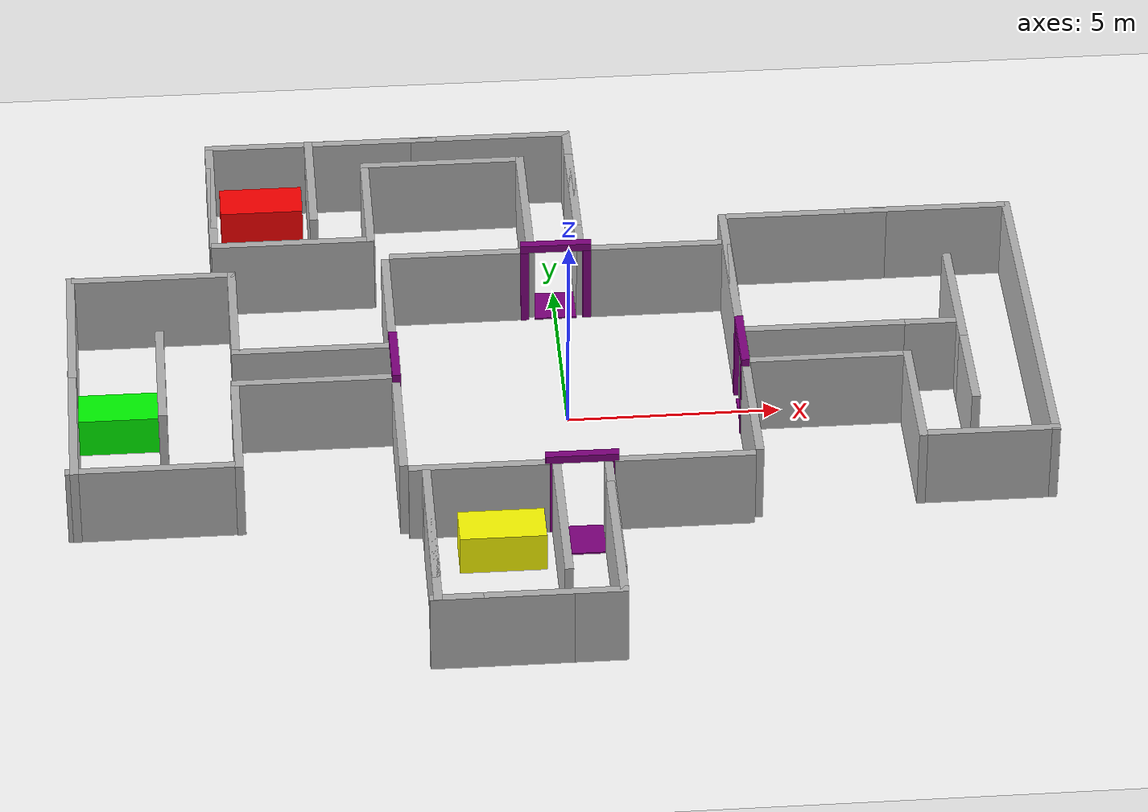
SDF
<?xml version="1.0" ?>
<sdf version='1.7'>
  <world name='laberinto_v2_world'>
    <plugin name='gz::sim::systems::Physics' filename='gz-sim-physics-system'/>
    <plugin name='gz::sim::systems::UserCommands' filename='gz-sim-user-commands-system'/>
    <plugin name='gz::sim::systems::SceneBroadcaster' filename='gz-sim-scene-broadcaster-system'/>
    <plugin name='gz::sim::systems::Imu' filename='gz-sim-imu-system'/>
    <plugin name='gz::sim::systems::Sensors' filename='gz-sim-sensors-system'>
      <render_engine>ogre2</render_engine>
    </plugin>
    <gravity>0 0 -9.8000000000000007</gravity>
    <magnetic_field>5.5644999999999998e-06 2.2875799999999999e-05 -4.2388400000000002e-05</magnetic_field>
    <atmosphere type='adiabatic'/>
    <physics type='ode'>
      <max_step_size>0.001</max_step_size>
      <real_time_factor>1</real_time_factor>
      <real_time_update_rate>1000</real_time_update_rate>
    </physics>
    <scene>
      <ambient>0.400000006 0.400000006 0.400000006 1</ambient>
      <background>0.699999988 0.699999988 0.699999988 1</background>
      <shadows>true</shadows>
    </scene>
    <model name='white_floor'>
      <static>true</static>
      <pose>0 0 0 0 0 0</pose>
      <link name='floor_link'>
        <collision name='collision'>
          <geometry>
            <plane>
              <normal>0 0 1</normal>
              <size>40 40</size>
            </plane>
          </geometry>
          <surface>
            <friction>
              <ode/>
            </friction>
            <bounce/>
            <contact/>
          </surface>
        </collision>
        <visual name='visual'>
          <geometry>
            <plane>
              <normal>0 0 1</normal>
              <size>40 40</size>
            </plane>
          </geometry>
          <material>
            <ambient>1 1 1 1</ambient>
            <diffuse>1 1 1 1</diffuse>
            <specular>0.100000001 0.100000001 0.100000001 1</specular>
          </material>
        </visual>
        <pose>0 0 0 0 0 0</pose>
        <inertial>
          <pose>0 0 0 0 0 0</pose>
          <mass>1</mass>
          <inertia>
            <ixx>1</ixx>
            <ixy>0</ixy>
            <ixz>0</ixz>
            <iyy>1</iyy>
            <iyz>0</iyz>
            <izz>1</izz>
          </inertia>
        </inertial>
        <enable_wind>false</enable_wind>
      </link>
      <self_collide>false</self_collide>
    </model>
    <model name='central_wall_north_left'>
      <static>true</static>
      <pose>-2.375 4.0999999999999996 1 0 0 0</pose>
      <link name='link'>
        <collision name='collision'>
          <geometry>
            <box>
              <size>3.25 0.20000000000000001 2</size>
            </box>
          </geometry>
          <surface>
            <friction>
              <ode/>
            </friction>
            <bounce/>
            <contact/>
          </surface>
        </collision>
        <visual name='visual'>
          <geometry>
            <box>
              <size>3.25 0.20000000000000001 2</size>
            </box>
          </geometry>
          <material>
            <ambient>0.699999988 0.699999988 0.699999988 1</ambient>
            <diffuse>0.699999988 0.699999988 0.699999988 1</diffuse>
          </material>
        </visual>
        <pose>0 0 0 0 0 0</pose>
        <inertial>
          <pose>0 0 0 0 0 0</pose>
          <mass>1</mass>
          <inertia>
            <ixx>1</ixx>
            <ixy>0</ixy>
            <ixz>0</ixz>
            <iyy>1</iyy>
            <iyz>0</iyz>
            <izz>1</izz>
          </inertia>
        </inertial>
        <enable_wind>false</enable_wind>
      </link>
      <self_collide>false</self_collide>
    </model>
    <model name='central_wall_north_right'>
      <static>true</static>
      <pose>2.375 4.0999999999999996 1 0 0 0</pose>
      <link name='link'>
        <collision name='collision'>
          <geometry>
            <box>
              <size>3.25 0.20000000000000001 2</size>
            </box>
          </geometry>
          <surface>
            <friction>
              <ode/>
            </friction>
            <bounce/>
            <contact/>
          </surface>
        </collision>
        <visual name='visual'>
          <geometry>
            <box>
              <size>3.25 0.20000000000000001 2</size>
            </box>
          </geometry>
          <material>
            <ambient>0.699999988 0.699999988 0.699999988 1</ambient>
            <diffuse>0.699999988 0.699999988 0.699999988 1</diffuse>
          </material>
        </visual>
        <pose>0 0 0 0 0 0</pose>
        <inertial>
          <pose>0 0 0 0 0 0</pose>
          <mass>1</mass>
          <inertia>
            <ixx>1</ixx>
            <ixy>0</ixy>
            <ixz>0</ixz>
            <iyy>1</iyy>
            <iyz>0</iyz>
            <izz>1</izz>
          </inertia>
        </inertial>
        <enable_wind>false</enable_wind>
      </link>
      <self_collide>false</self_collide>
    </model>
    <model name='central_wall_south_left'>
      <static>true</static>
      <pose>-2.375 -4.0999999999999996 1 0 0 0</pose>
      <link name='link'>
        <collision name='collision'>
          <geometry>
            <box>
              <size>3.25 0.20000000000000001 2</size>
            </box>
          </geometry>
          <surface>
            <friction>
              <ode/>
            </friction>
            <bounce/>
            <contact/>
          </surface>
        </collision>
        <visual name='visual'>
          <geometry>
            <box>
              <size>3.25 0.20000000000000001 2</size>
            </box>
          </geometry>
          <material>
            <ambient>0.699999988 0.699999988 0.699999988 1</ambient>
            <diffuse>0.699999988 0.699999988 0.699999988 1</diffuse>
          </material>
        </visual>
        <pose>0 0 0 0 0 0</pose>
        <inertial>
          <pose>0 0 0 0 0 0</pose>
          <mass>1</mass>
          <inertia>
            <ixx>1</ixx>
            <ixy>0</ixy>
            <ixz>0</ixz>
            <iyy>1</iyy>
            <iyz>0</iyz>
            <izz>1</izz>
          </inertia>
        </inertial>
        <enable_wind>false</enable_wind>
      </link>
      <self_collide>false</self_collide>
    </model>
    <model name='central_wall_south_right'>
      <static>true</static>
      <pose>2.375 -4.0999999999999996 1 0 0 0</pose>
      <link name='link'>
        <collision name='collision'>
          <geometry>
            <box>
              <size>3.25 0.20000000000000001 2</size>
            </box>
          </geometry>
          <surface>
            <friction>
              <ode/>
            </friction>
            <bounce/>
            <contact/>
          </surface>
        </collision>
        <visual name='visual'>
          <geometry>
            <box>
              <size>3.25 0.20000000000000001 2</size>
            </box>
          </geometry>
          <material>
            <ambient>0.699999988 0.699999988 0.699999988 1</ambient>
            <diffuse>0.699999988 0.699999988 0.699999988 1</diffuse>
          </material>
        </visual>
        <pose>0 0 0 0 0 0</pose>
        <inertial>
          <pose>0 0 0 0 0 0</pose>
          <mass>1</mass>
          <inertia>
            <ixx>1</ixx>
            <ixy>0</ixy>
            <ixz>0</ixz>
            <iyy>1</iyy>
            <iyz>0</iyz>
            <izz>1</izz>
          </inertia>
        </inertial>
        <enable_wind>false</enable_wind>
      </link>
      <self_collide>false</self_collide>
    </model>
    <model name='central_wall_east_bottom'>
      <static>true</static>
      <pose>4.0999999999999996 -2.375 1 0 0 0</pose>
      <link name='link'>
        <collision name='collision'>
          <geometry>
            <box>
              <size>0.20000000000000001 3.25 2</size>
            </box>
          </geometry>
          <surface>
            <friction>
              <ode/>
            </friction>
            <bounce/>
            <contact/>
          </surface>
        </collision>
        <visual name='visual'>
          <geometry>
            <box>
              <size>0.20000000000000001 3.25 2</size>
            </box>
          </geometry>
          <material>
            <ambient>0.699999988 0.699999988 0.699999988 1</ambient>
            <diffuse>0.699999988 0.699999988 0.699999988 1</diffuse>
          </material>
        </visual>
        <pose>0 0 0 0 0 0</pose>
        <inertial>
          <pose>0 0 0 0 0 0</pose>
          <mass>1</mass>
          <inertia>
            <ixx>1</ixx>
            <ixy>0</ixy>
            <ixz>0</ixz>
            <iyy>1</iyy>
            <iyz>0</iyz>
            <izz>1</izz>
          </inertia>
        </inertial>
        <enable_wind>false</enable_wind>
      </link>
      <self_collide>false</self_collide>
    </model>
    <model name='central_wall_east_top'>
      <static>true</static>
      <pose>4.0999999999999996 2.375 1 0 0 0</pose>
      <link name='link'>
        <collision name='collision'>
          <geometry>
            <box>
              <size>0.20000000000000001 3.25 2</size>
            </box>
          </geometry>
          <surface>
            <friction>
              <ode/>
            </friction>
            <bounce/>
            <contact/>
          </surface>
        </collision>
        <visual name='visual'>
          <geometry>
            <box>
              <size>0.20000000000000001 3.25 2</size>
            </box>
          </geometry>
          <material>
            <ambient>0.699999988 0.699999988 0.699999988 1</ambient>
            <diffuse>0.699999988 0.699999988 0.699999988 1</diffuse>
          </material>
        </visual>
        <pose>0 0 0 0 0 0</pose>
        <inertial>
          <pose>0 0 0 0 0 0</pose>
          <mass>1</mass>
          <inertia>
            <ixx>1</ixx>
            <ixy>0</ixy>
            <ixz>0</ixz>
            <iyy>1</iyy>
            <iyz>0</iyz>
            <izz>1</izz>
          </inertia>
        </inertial>
        <enable_wind>false</enable_wind>
      </link>
      <self_collide>false</self_collide>
    </model>
    <model name='central_wall_west_bottom'>
      <static>true</static>
      <pose>-4.0999999999999996 -2.375 1 0 0 0</pose>
      <link name='link'>
        <collision name='collision'>
          <geometry>
            <box>
              <size>0.20000000000000001 3.25 2</size>
            </box>
          </geometry>
          <surface>
            <friction>
              <ode/>
            </friction>
            <bounce/>
            <contact/>
          </surface>
        </collision>
        <visual name='visual'>
          <geometry>
            <box>
              <size>0.20000000000000001 3.25 2</size>
            </box>
          </geometry>
          <material>
            <ambient>0.699999988 0.699999988 0.699999988 1</ambient>
            <diffuse>0.699999988 0.699999988 0.699999988 1</diffuse>
          </material>
        </visual>
        <pose>0 0 0 0 0 0</pose>
        <inertial>
          <pose>0 0 0 0 0 0</pose>
          <mass>1</mass>
          <inertia>
            <ixx>1</ixx>
            <ixy>0</ixy>
            <ixz>0</ixz>
            <iyy>1</iyy>
            <iyz>0</iyz>
            <izz>1</izz>
          </inertia>
        </inertial>
        <enable_wind>false</enable_wind>
      </link>
      <self_collide>false</self_collide>
    </model>
    <model name='central_wall_west_top'>
      <static>true</static>
      <pose>-4.0999999999999996 2.375 1 0 0 0</pose>
      <link name='link'>
        <collision name='collision'>
          <geometry>
            <box>
              <size>0.20000000000000001 3.25 2</size>
            </box>
          </geometry>
          <surface>
            <friction>
              <ode/>
            </friction>
            <bounce/>
            <contact/>
          </surface>
        </collision>
        <visual name='visual'>
          <geometry>
            <box>
              <size>0.20000000000000001 3.25 2</size>
            </box>
          </geometry>
          <material>
            <ambient>0.699999988 0.699999988 0.699999988 1</ambient>
            <diffuse>0.699999988 0.699999988 0.699999988 1</diffuse>
          </material>
        </visual>
        <pose>0 0 0 0 0 0</pose>
        <inertial>
          <pose>0 0 0 0 0 0</pose>
          <mass>1</mass>
          <inertia>
            <ixx>1</ixx>
            <ixy>0</ixy>
            <ixz>0</ixz>
            <iyy>1</iyy>
            <iyz>0</iyz>
            <izz>1</izz>
          </inertia>
        </inertial>
        <enable_wind>false</enable_wind>
      </link>
      <self_collide>false</self_collide>
    </model>
    <model name='purple_carpet_north'>
      <static>true</static>
      <pose>0 4.5239000000000003 -0.0097000000000000003 0 0 0</pose>
      <link name='link'>
        <collision name='collision'>
          <geometry>
            <box>
              <size>1 1 0.050000000000000003</size>
            </box>
          </geometry>
          <surface>
            <friction>
              <ode/>
            </friction>
            <bounce/>
            <contact/>
          </surface>
        </collision>
        <visual name='visual'>
          <geometry>
            <box>
              <size>1 1 0.050000000000000003</size>
            </box>
          </geometry>
          <material>
            <ambient>0.5 0 0.5 1</ambient>
            <diffuse>0.5 0 0.5 1</diffuse>
          </material>
        </visual>
        <pose>0 0 0 0 0 0</pose>
        <inertial>
          <pose>0 0 0 0 0 0</pose>
          <mass>1</mass>
          <inertia>
            <ixx>1</ixx>
            <ixy>0</ixy>
            <ixz>0</ixz>
            <iyy>1</iyy>
            <iyz>0</iyz>
            <izz>1</izz>
          </inertia>
        </inertial>
        <enable_wind>false</enable_wind>
      </link>
      <self_collide>false</self_collide>
    </model>
    <model name='purple_carpet_south'>
      <static>true</static>
      <pose>0 -4.5239000000000003 -0.0097000000000000003 0 0 0</pose>
      <link name='link'>
        <collision name='collision'>
          <geometry>
            <box>
              <size>1 1 0.050000000000000003</size>
            </box>
          </geometry>
          <surface>
            <friction>
              <ode/>
            </friction>
            <bounce/>
            <contact/>
          </surface>
        </collision>
        <visual name='visual'>
          <geometry>
            <box>
              <size>1 1 0.050000000000000003</size>
            </box>
          </geometry>
          <material>
            <ambient>0.5 0 0.5 1</ambient>
            <diffuse>0.5 0 0.5 1</diffuse>
          </material>
        </visual>
        <pose>0 0 0 0 0 0</pose>
        <inertial>
          <pose>0 0 0 0 0 0</pose>
          <mass>1</mass>
          <inertia>
            <ixx>1</ixx>
            <ixy>0</ixy>
            <ixz>0</ixz>
            <iyy>1</iyy>
            <iyz>0</iyz>
            <izz>1</izz>
          </inertia>
        </inertial>
        <enable_wind>false</enable_wind>
      </link>
      <self_collide>false</self_collide>
    </model>
    <model name='purple_carpet_east'>
      <static>true</static>
      <pose>4.5239000000000003 0 -0.0097000000000000003 0 0 0</pose>
      <link name='link'>
        <collision name='collision'>
          <geometry>
            <box>
              <size>1 1 0.050000000000000003</size>
            </box>
          </geometry>
          <surface>
            <friction>
              <ode/>
            </friction>
            <bounce/>
            <contact/>
          </surface>
        </collision>
        <visual name='visual'>
          <geometry>
            <box>
              <size>1 1 0.050000000000000003</size>
            </box>
          </geometry>
          <material>
            <ambient>0.5 0 0.5 1</ambient>
            <diffuse>0.5 0 0.5 1</diffuse>
          </material>
        </visual>
        <pose>0 0 0 0 0 0</pose>
        <inertial>
          <pose>0 0 0 0 0 0</pose>
          <mass>1</mass>
          <inertia>
            <ixx>1</ixx>
            <ixy>0</ixy>
            <ixz>0</ixz>
            <iyy>1</iyy>
            <iyz>0</iyz>
            <izz>1</izz>
          </inertia>
        </inertial>
        <enable_wind>false</enable_wind>
      </link>
      <self_collide>false</self_collide>
    </model>
    <model name='purple_carpet_west'>
      <static>true</static>
      <pose>-4.5239000000000003 0 -0.0097000000000000003 0 0 0</pose>
      <link name='link'>
        <collision name='collision'>
          <geometry>
            <box>
              <size>1 1 0.050000000000000003</size>
            </box>
          </geometry>
          <surface>
            <friction>
              <ode/>
            </friction>
            <bounce/>
            <contact/>
          </surface>
        </collision>
        <visual name='visual'>
          <geometry>
            <box>
              <size>1 1 0.050000000000000003</size>
            </box>
          </geometry>
          <material>
            <ambient>0.5 0 0.5 1</ambient>
            <diffuse>0.5 0 0.5 1</diffuse>
          </material>
        </visual>
        <pose>0 0 0 0 0 0</pose>
        <inertial>
          <pose>0 0 0 0 0 0</pose>
          <mass>1</mass>
          <inertia>
            <ixx>1</ixx>
            <ixy>0</ixy>
            <ixz>0</ixz>
            <iyy>1</iyy>
            <iyz>0</iyz>
            <izz>1</izz>
          </inertia>
        </inertial>
        <enable_wind>false</enable_wind>
      </link>
      <self_collide>false</self_collide>
    </model>
    <model name='roman_arch_north'>
      <static>true</static>
      <pose>0 4.0841000000000003 0 0 0 0</pose>
      <link name='pillar_left'>
        <pose>-0.75 0 1 0 0 0</pose>
        <collision name='collision'>
          <geometry>
            <box>
              <size>0.20000000000000001 0.20000000000000001 2</size>
            </box>
          </geometry>
          <surface>
            <friction>
              <ode/>
            </friction>
            <bounce/>
            <contact/>
          </surface>
        </collision>
        <visual name='visual'>
          <geometry>
            <box>
              <size>0.20000000000000001 0.20000000000000001 2</size>
            </box>
          </geometry>
          <material>
            <ambient>0.5 0 0.5 1</ambient>
            <diffuse>0.5 0 0.5 1</diffuse>
          </material>
        </visual>
        <inertial>
          <pose>0 0 0 0 0 0</pose>
          <mass>1</mass>
          <inertia>
            <ixx>1</ixx>
            <ixy>0</ixy>
            <ixz>0</ixz>
            <iyy>1</iyy>
            <iyz>0</iyz>
            <izz>1</izz>
          </inertia>
        </inertial>
        <enable_wind>false</enable_wind>
      </link>
      <link name='pillar_right'>
        <pose>0.75 0 1 0 0 0</pose>
        <collision name='collision'>
          <geometry>
            <box>
              <size>0.20000000000000001 0.20000000000000001 2</size>
            </box>
          </geometry>
          <surface>
            <friction>
              <ode/>
            </friction>
            <bounce/>
            <contact/>
          </surface>
        </collision>
        <visual name='visual'>
          <geometry>
            <box>
              <size>0.20000000000000001 0.20000000000000001 2</size>
            </box>
          </geometry>
          <material>
            <ambient>0.5 0 0.5 1</ambient>
            <diffuse>0.5 0 0.5 1</diffuse>
          </material>
        </visual>
        <inertial>
          <pose>0 0 0 0 0 0</pose>
          <mass>1</mass>
          <inertia>
            <ixx>1</ixx>
            <ixy>0</ixy>
            <ixz>0</ixz>
            <iyy>1</iyy>
            <iyz>0</iyz>
            <izz>1</izz>
          </inertia>
        </inertial>
        <enable_wind>false</enable_wind>
      </link>
      <link name='arch_top'>
        <pose>0 0 2.1000000000000001 0 0 0</pose>
        <collision name='collision'>
          <geometry>
            <box>
              <size>1.7 0.20000000000000001 0.20000000000000001</size>
            </box>
          </geometry>
          <surface>
            <friction>
              <ode/>
            </friction>
            <bounce/>
            <contact/>
          </surface>
        </collision>
        <visual name='visual'>
          <geometry>
            <box>
              <size>1.7 0.20000000000000001 0.20000000000000001</size>
            </box>
          </geometry>
          <material>
            <ambient>0.5 0 0.5 1</ambient>
            <diffuse>0.5 0 0.5 1</diffuse>
          </material>
        </visual>
        <inertial>
          <pose>0 0 0 0 0 0</pose>
          <mass>1</mass>
          <inertia>
            <ixx>1</ixx>
            <ixy>0</ixy>
            <ixz>0</ixz>
            <iyy>1</iyy>
            <iyz>0</iyz>
            <izz>1</izz>
          </inertia>
        </inertial>
        <enable_wind>false</enable_wind>
      </link>
      <self_collide>false</self_collide>
    </model>
    <model name='roman_arch_south'>
      <static>true</static>
      <pose>0 -4.0841000000000003 0 0 0 0</pose>
      <link name='pillar_left'>
        <pose>-0.75 0 1 0 0 0</pose>
        <collision name='collision'>
          <geometry>
            <box>
              <size>0.20000000000000001 0.20000000000000001 2</size>
            </box>
          </geometry>
          <surface>
            <friction>
              <ode/>
            </friction>
            <bounce/>
            <contact/>
          </surface>
        </collision>
        <visual name='visual'>
          <geometry>
            <box>
              <size>0.20000000000000001 0.20000000000000001 2</size>
            </box>
          </geometry>
          <material>
            <ambient>0.5 0 0.5 1</ambient>
            <diffuse>0.5 0 0.5 1</diffuse>
          </material>
        </visual>
        <inertial>
          <pose>0 0 0 0 0 0</pose>
          <mass>1</mass>
          <inertia>
            <ixx>1</ixx>
            <ixy>0</ixy>
            <ixz>0</ixz>
            <iyy>1</iyy>
            <iyz>0</iyz>
            <izz>1</izz>
          </inertia>
        </inertial>
        <enable_wind>false</enable_wind>
      </link>
      <link name='pillar_right'>
        <pose>0.75 0 1 0 0 0</pose>
        <collision name='collision'>
          <geometry>
            <box>
              <size>0.20000000000000001 0.20000000000000001 2</size>
            </box>
          </geometry>
          <surface>
            <friction>
              <ode/>
            </friction>
            <bounce/>
            <contact/>
          </surface>
        </collision>
        <visual name='visual'>
          <geometry>
            <box>
              <size>0.20000000000000001 0.20000000000000001 2</size>
            </box>
          </geometry>
          <material>
            <ambient>0.5 0 0.5 1</ambient>
            <diffuse>0.5 0 0.5 1</diffuse>
          </material>
        </visual>
        <inertial>
          <pose>0 0 0 0 0 0</pose>
          <mass>1</mass>
          <inertia>
            <ixx>1</ixx>
            <ixy>0</ixy>
            <ixz>0</ixz>
            <iyy>1</iyy>
            <iyz>0</iyz>
            <izz>1</izz>
          </inertia>
        </inertial>
        <enable_wind>false</enable_wind>
      </link>
      <link name='arch_top'>
        <pose>0 0 2.1000000000000001 0 0 0</pose>
        <collision name='collision'>
          <geometry>
            <box>
              <size>1.7 0.20000000000000001 0.20000000000000001</size>
            </box>
          </geometry>
          <surface>
            <friction>
              <ode/>
            </friction>
            <bounce/>
            <contact/>
          </surface>
        </collision>
        <visual name='visual'>
          <geometry>
            <box>
              <size>1.7 0.20000000000000001 0.20000000000000001</size>
            </box>
          </geometry>
          <material>
            <ambient>0.5 0 0.5 1</ambient>
            <diffuse>0.5 0 0.5 1</diffuse>
          </material>
        </visual>
        <inertial>
          <pose>0 0 0 0 0 0</pose>
          <mass>1</mass>
          <inertia>
            <ixx>1</ixx>
            <ixy>0</ixy>
            <ixz>0</ixz>
            <iyy>1</iyy>
            <iyz>0</iyz>
            <izz>1</izz>
          </inertia>
        </inertial>
        <enable_wind>false</enable_wind>
      </link>
      <self_collide>false</self_collide>
    </model>
    <model name='roman_arch_east'>
      <static>true</static>
      <pose>4.0841000000000003 -1.1102230246251565e-16 0 0 0 1.5708000000000006</pose>
      <link name='pillar_left'>
        <pose>-0.75 0 1 0 0 0</pose>
        <collision name='collision'>
          <geometry>
            <box>
              <size>0.20000000000000001 0.20000000000000001 2</size>
            </box>
          </geometry>
          <surface>
            <friction>
              <ode/>
            </friction>
            <bounce/>
            <contact/>
          </surface>
        </collision>
        <visual name='visual'>
          <geometry>
            <box>
              <size>0.20000000000000001 0.20000000000000001 2</size>
            </box>
          </geometry>
          <material>
            <ambient>0.5 0 0.5 1</ambient>
            <diffuse>0.5 0 0.5 1</diffuse>
          </material>
        </visual>
        <inertial>
          <pose>0 0 0 0 0 0</pose>
          <mass>1</mass>
          <inertia>
            <ixx>1</ixx>
            <ixy>0</ixy>
            <ixz>0</ixz>
            <iyy>1</iyy>
            <iyz>0</iyz>
            <izz>1</izz>
          </inertia>
        </inertial>
        <enable_wind>false</enable_wind>
      </link>
      <link name='pillar_right'>
        <pose>0.74999999999999978 0 1 0 0 0</pose>
        <collision name='collision'>
          <geometry>
            <box>
              <size>0.20000000000000001 0.20000000000000001 2</size>
            </box>
          </geometry>
          <surface>
            <friction>
              <ode/>
            </friction>
            <bounce/>
            <contact/>
          </surface>
        </collision>
        <visual name='visual'>
          <geometry>
            <box>
              <size>0.20000000000000001 0.20000000000000001 2</size>
            </box>
          </geometry>
          <material>
            <ambient>0.5 0 0.5 1</ambient>
            <diffuse>0.5 0 0.5 1</diffuse>
          </material>
        </visual>
        <inertial>
          <pose>0 0 0 0 0 0</pose>
          <mass>1</mass>
          <inertia>
            <ixx>1</ixx>
            <ixy>0</ixy>
            <ixz>0</ixz>
            <iyy>1</iyy>
            <iyz>0</iyz>
            <izz>1</izz>
          </inertia>
        </inertial>
        <enable_wind>false</enable_wind>
      </link>
      <link name='arch_top'>
        <pose>0 0 2.1000000000000005 0 0 0</pose>
        <collision name='collision'>
          <geometry>
            <box>
              <size>1.7 0.20000000000000001 0.20000000000000001</size>
            </box>
          </geometry>
          <surface>
            <friction>
              <ode/>
            </friction>
            <bounce/>
            <contact/>
          </surface>
        </collision>
        <visual name='visual'>
          <geometry>
            <box>
              <size>1.7 0.20000000000000001 0.20000000000000001</size>
            </box>
          </geometry>
          <material>
            <ambient>0.5 0 0.5 1</ambient>
            <diffuse>0.5 0 0.5 1</diffuse>
          </material>
        </visual>
        <inertial>
          <pose>0 0 0 0 0 0</pose>
          <mass>1</mass>
          <inertia>
            <ixx>1</ixx>
            <ixy>0</ixy>
            <ixz>0</ixz>
            <iyy>1</iyy>
            <iyz>0</iyz>
            <izz>1</izz>
          </inertia>
        </inertial>
        <enable_wind>false</enable_wind>
      </link>
      <self_collide>false</self_collide>
    </model>
    <model name='roman_arch_west'>
      <static>true</static>
      <pose>-4.0841000000000003 -1.1102230246251565e-16 0 0 0 1.5708000000000006</pose>
      <link name='pillar_left'>
        <pose>-0.75 0 1 0 0 0</pose>
        <collision name='collision'>
          <geometry>
            <box>
              <size>0.20000000000000001 0.20000000000000001 2</size>
            </box>
          </geometry>
          <surface>
            <friction>
              <ode/>
            </friction>
            <bounce/>
            <contact/>
          </surface>
        </collision>
        <visual name='visual'>
          <geometry>
            <box>
              <size>0.20000000000000001 0.20000000000000001 2</size>
            </box>
          </geometry>
          <material>
            <ambient>0.5 0 0.5 1</ambient>
            <diffuse>0.5 0 0.5 1</diffuse>
          </material>
        </visual>
        <inertial>
          <pose>0 0 0 0 0 0</pose>
          <mass>1</mass>
          <inertia>
            <ixx>1</ixx>
            <ixy>0</ixy>
            <ixz>0</ixz>
            <iyy>1</iyy>
            <iyz>0</iyz>
            <izz>1</izz>
          </inertia>
        </inertial>
        <enable_wind>false</enable_wind>
      </link>
      <link name='pillar_right'>
        <pose>0.75000000000000044 0 1 0 0 0</pose>
        <collision name='collision'>
          <geometry>
            <box>
              <size>0.20000000000000001 0.20000000000000001 2</size>
            </box>
          </geometry>
          <surface>
            <friction>
              <ode/>
            </friction>
            <bounce/>
            <contact/>
          </surface>
        </collision>
        <visual name='visual'>
          <geometry>
            <box>
              <size>0.20000000000000001 0.20000000000000001 2</size>
            </box>
          </geometry>
          <material>
            <ambient>0.5 0 0.5 1</ambient>
            <diffuse>0.5 0 0.5 1</diffuse>
          </material>
        </visual>
        <inertial>
          <pose>0 0 0 0 0 0</pose>
          <mass>1</mass>
          <inertia>
            <ixx>1</ixx>
            <ixy>0</ixy>
            <ixz>0</ixz>
            <iyy>1</iyy>
            <iyz>0</iyz>
            <izz>1</izz>
          </inertia>
        </inertial>
        <enable_wind>false</enable_wind>
      </link>
      <link name='arch_top'>
        <pose>0 0 2.1000000000000005 0 0 0</pose>
        <collision name='collision'>
          <geometry>
            <box>
              <size>1.7 0.20000000000000001 0.20000000000000001</size>
            </box>
          </geometry>
          <surface>
            <friction>
              <ode/>
            </friction>
            <bounce/>
            <contact/>
          </surface>
        </collision>
        <visual name='visual'>
          <geometry>
            <box>
              <size>1.7 0.20000000000000001 0.20000000000000001</size>
            </box>
          </geometry>
          <material>
            <ambient>0.5 0 0.5 1</ambient>
            <diffuse>0.5 0 0.5 1</diffuse>
          </material>
        </visual>
        <inertial>
          <pose>0 0 0 0 0 0</pose>
          <mass>1</mass>
          <inertia>
            <ixx>1</ixx>
            <ixy>0</ixy>
            <ixz>0</ixz>
            <iyy>1</iyy>
            <iyz>0</iyz>
            <izz>1</izz>
          </inertia>
        </inertial>
        <enable_wind>false</enable_wind>
      </link>
      <self_collide>false</self_collide>
    </model>
    <model name='hall_N_seg1_wall_W'>
      <static>true</static>
      <pose>-0.59999999999999998 6.0499999999999998 1 0 0 0</pose>
      <link name='link'>
        <collision name='collision'>
          <geometry>
            <box>
              <size>0.20000000000000001 3.8999999999999999 2</size>
            </box>
          </geometry>
          <surface>
            <friction>
              <ode/>
            </friction>
            <bounce/>
            <contact/>
          </surface>
        </collision>
        <visual name='visual'>
          <geometry>
            <box>
              <size>0.20000000000000001 3.8999999999999999 2</size>
            </box>
          </geometry>
          <material>
            <ambient>0.699999988 0.699999988 0.699999988 1</ambient>
            <diffuse>0.699999988 0.699999988 0.699999988 1</diffuse>
          </material>
        </visual>
        <pose>0 0 0 0 0 0</pose>
        <inertial>
          <pose>0 0 0 0 0 0</pose>
          <mass>1</mass>
          <inertia>
            <ixx>1</ixx>
            <ixy>0</ixy>
            <ixz>0</ixz>
            <iyy>1</iyy>
            <iyz>0</iyz>
            <izz>1</izz>
          </inertia>
        </inertial>
        <enable_wind>false</enable_wind>
      </link>
      <self_collide>false</self_collide>
    </model>
    <model name='hall_N_seg1_wall_E'>
      <static>true</static>
      <pose>0.59999999999999998 6.0499999999999998 1 0 0 0</pose>
      <link name='link'>
        <collision name='collision'>
          <geometry>
            <box>
              <size>0.20000000000000001 3.8999999999999999 2</size>
            </box>
          </geometry>
          <surface>
            <friction>
              <ode/>
            </friction>
            <bounce/>
            <contact/>
          </surface>
        </collision>
        <visual name='visual'>
          <geometry>
            <box>
              <size>0.20000000000000001 3.8999999999999999 2</size>
            </box>
          </geometry>
          <material>
            <ambient>0.699999988 0.699999988 0.699999988 1</ambient>
            <diffuse>0.699999988 0.699999988 0.699999988 1</diffuse>
          </material>
        </visual>
        <pose>0 0 0 0 0 0</pose>
        <inertial>
          <pose>0 0 0 0 0 0</pose>
          <mass>1</mass>
          <inertia>
            <ixx>1</ixx>
            <ixy>0</ixy>
            <ixz>0</ixz>
            <iyy>1</iyy>
            <iyz>0</iyz>
            <izz>1</izz>
          </inertia>
        </inertial>
        <enable_wind>false</enable_wind>
      </link>
      <self_collide>false</self_collide>
    </model>
    <model name='hall_E_seg1_wall_S'>
      <static>true</static>
      <pose>6.0499999999999998 -0.59999999999999998 1 0 0 0</pose>
      <link name='link'>
        <collision name='collision'>
          <geometry>
            <box>
              <size>3.8999999999999999 0.20000000000000001 2</size>
            </box>
          </geometry>
          <surface>
            <friction>
              <ode/>
            </friction>
            <bounce/>
            <contact/>
          </surface>
        </collision>
        <visual name='visual'>
          <geometry>
            <box>
              <size>3.8999999999999999 0.20000000000000001 2</size>
            </box>
          </geometry>
          <material>
            <ambient>0.699999988 0.699999988 0.699999988 1</ambient>
            <diffuse>0.699999988 0.699999988 0.699999988 1</diffuse>
          </material>
        </visual>
        <pose>0 0 0 0 0 0</pose>
        <inertial>
          <pose>0 0 0 0 0 0</pose>
          <mass>1</mass>
          <inertia>
            <ixx>1</ixx>
            <ixy>0</ixy>
            <ixz>0</ixz>
            <iyy>1</iyy>
            <iyz>0</iyz>
            <izz>1</izz>
          </inertia>
        </inertial>
        <enable_wind>false</enable_wind>
      </link>
      <self_collide>false</self_collide>
    </model>
    <model name='hall_E_seg1_wall_N'>
      <static>true</static>
      <pose>6.0499999999999998 0.59999999999999998 1 0 0 0</pose>
      <link name='link'>
        <collision name='collision'>
          <geometry>
            <box>
              <size>3.8999999999999999 0.20000000000000001 2</size>
            </box>
          </geometry>
          <surface>
            <friction>
              <ode/>
            </friction>
            <bounce/>
            <contact/>
          </surface>
        </collision>
        <visual name='visual'>
          <geometry>
            <box>
              <size>3.8999999999999999 0.20000000000000001 2</size>
            </box>
          </geometry>
          <material>
            <ambient>0.699999988 0.699999988 0.699999988 1</ambient>
            <diffuse>0.699999988 0.699999988 0.699999988 1</diffuse>
          </material>
        </visual>
        <pose>0 0 0 0 0 0</pose>
        <inertial>
          <pose>0 0 0 0 0 0</pose>
          <mass>1</mass>
          <inertia>
            <ixx>1</ixx>
            <ixy>0</ixy>
            <ixz>0</ixz>
            <iyy>1</iyy>
            <iyz>0</iyz>
            <izz>1</izz>
          </inertia>
        </inertial>
        <enable_wind>false</enable_wind>
      </link>
      <self_collide>false</self_collide>
    </model>
    <model name='hall_E_turn_wall_E'>
      <static>true</static>
      <pose>8.6907930374145508 0.59337317943572998 1 0 0 1.5708000357176291</pose>
      <link name='link'>
        <collision name='collision'>
          <geometry>
            <box>
              <size>0.20000000000000001 1.3999999999999999 2</size>
            </box>
          </geometry>
          <surface>
            <friction>
              <ode/>
            </friction>
            <bounce/>
            <contact/>
          </surface>
        </collision>
        <visual name='visual'>
          <geometry>
            <box>
              <size>0.20000000000000001 1.3999999999999999 2</size>
            </box>
          </geometry>
          <material>
            <ambient>0.699999988 0.699999988 0.699999988 1</ambient>
            <diffuse>0.699999988 0.699999988 0.699999988 1</diffuse>
          </material>
        </visual>
        <pose>0 0 0 0 0 0</pose>
        <inertial>
          <pose>0 0 0 0 0 0</pose>
          <mass>1</mass>
          <inertia>
            <ixx>1</ixx>
            <ixy>0</ixy>
            <ixz>0</ixz>
            <iyy>1</iyy>
            <iyz>0</iyz>
            <izz>1</izz>
          </inertia>
        </inertial>
        <enable_wind>false</enable_wind>
      </link>
      <self_collide>false</self_collide>
    </model>
    <model name='hall_E_seg2_wall_W'>
      <static>true</static>
      <pose>11.001354217529297 0.73156499862670898 1 0 0 0</pose>
      <link name='link'>
        <collision name='collision'>
          <geometry>
            <box>
              <size>0.20000000000000001 9 2</size>
            </box>
          </geometry>
          <surface>
            <friction>
              <ode/>
            </friction>
            <bounce/>
            <contact/>
          </surface>
        </collision>
        <visual name='visual'>
          <geometry>
            <box>
              <size>0.20000000000000001 9 2</size>
            </box>
          </geometry>
          <material>
            <ambient>0.699999988 0.699999988 0.699999988 1</ambient>
            <diffuse>0.699999988 0.699999988 0.699999988 1</diffuse>
          </material>
        </visual>
        <pose>0 0 0 0 0 0</pose>
        <inertial>
          <pose>0 0 0 0 0 0</pose>
          <mass>1</mass>
          <inertia>
            <ixx>1</ixx>
            <ixy>0</ixy>
            <ixz>0</ixz>
            <iyy>1</iyy>
            <iyz>0</iyz>
            <izz>1</izz>
          </inertia>
        </inertial>
        <enable_wind>false</enable_wind>
      </link>
      <self_collide>false</self_collide>
    </model>
    <model name='hall_S_seg1_wall_W'>
      <static>true</static>
      <pose>-0.59999999999999998 -6.0499999999999998 1 0 0 0</pose>
      <link name='link'>
        <collision name='collision'>
          <geometry>
            <box>
              <size>0.20000000000000001 3.8999999999999999 2</size>
            </box>
          </geometry>
          <surface>
            <friction>
              <ode/>
            </friction>
            <bounce/>
            <contact/>
          </surface>
        </collision>
        <visual name='visual'>
          <geometry>
            <box>
              <size>0.20000000000000001 3.8999999999999999 2</size>
            </box>
          </geometry>
          <material>
            <ambient>0.699999988 0.699999988 0.699999988 1</ambient>
            <diffuse>0.699999988 0.699999988 0.699999988 1</diffuse>
          </material>
        </visual>
        <pose>0 0 0 0 0 0</pose>
        <inertial>
          <pose>0 0 0 0 0 0</pose>
          <mass>1</mass>
          <inertia>
            <ixx>1</ixx>
            <ixy>0</ixy>
            <ixz>0</ixz>
            <iyy>1</iyy>
            <iyz>0</iyz>
            <izz>1</izz>
          </inertia>
        </inertial>
        <enable_wind>false</enable_wind>
      </link>
      <self_collide>false</self_collide>
    </model>
    <model name='hall_S_seg1_wall_E'>
      <static>true</static>
      <pose>0.59999999999999998 -6.0499999999999998 1 0 0 0</pose>
      <link name='link'>
        <collision name='collision'>
          <geometry>
            <box>
              <size>0.20000000000000001 3.8999999999999999 2</size>
            </box>
          </geometry>
          <surface>
            <friction>
              <ode/>
            </friction>
            <bounce/>
            <contact/>
          </surface>
        </collision>
        <visual name='visual'>
          <geometry>
            <box>
              <size>0.20000000000000001 3.8999999999999999 2</size>
            </box>
          </geometry>
          <material>
            <ambient>0.699999988 0.699999988 0.699999988 1</ambient>
            <diffuse>0.699999988 0.699999988 0.699999988 1</diffuse>
          </material>
        </visual>
        <pose>0 0 0 0 0 0</pose>
        <inertial>
          <pose>0 0 0 0 0 0</pose>
          <mass>1</mass>
          <inertia>
            <ixx>1</ixx>
            <ixy>0</ixy>
            <ixz>0</ixz>
            <iyy>1</iyy>
            <iyz>0</iyz>
            <izz>1</izz>
          </inertia>
        </inertial>
        <enable_wind>false</enable_wind>
      </link>
      <self_collide>false</self_collide>
    </model>
    <model name='hall_W_seg1_wall_S'>
      <static>true</static>
      <pose>-5.9732098579406738 -0.60000002384185791 1 0 0 0</pose>
      <link name='link'>
        <collision name='collision'>
          <geometry>
            <box>
              <size>3.8999999999999999 0.20000000000000001 2</size>
            </box>
          </geometry>
          <surface>
            <friction>
              <ode/>
            </friction>
            <bounce/>
            <contact/>
          </surface>
        </collision>
        <visual name='visual'>
          <geometry>
            <box>
              <size>3.8999999999999999 0.20000000000000001 2</size>
            </box>
          </geometry>
          <material>
            <ambient>0.699999988 0.699999988 0.699999988 1</ambient>
            <diffuse>0.699999988 0.699999988 0.699999988 1</diffuse>
          </material>
        </visual>
        <pose>0 0 0 0 0 0</pose>
        <inertial>
          <pose>0 0 0 0 0 0</pose>
          <mass>1</mass>
          <inertia>
            <ixx>1</ixx>
            <ixy>0</ixy>
            <ixz>0</ixz>
            <iyy>1</iyy>
            <iyz>0</iyz>
            <izz>1</izz>
          </inertia>
        </inertial>
        <enable_wind>false</enable_wind>
      </link>
      <self_collide>false</self_collide>
    </model>
    <model name='hall_W_seg1_wall_N'>
      <static>true</static>
      <pose>-5.9408130645751953 0.60000002384185791 1 0 0 0</pose>
      <link name='link'>
        <collision name='collision'>
          <geometry>
            <box>
              <size>3.8999999999999999 0.20000000000000001 2</size>
            </box>
          </geometry>
          <surface>
            <friction>
              <ode/>
            </friction>
            <bounce/>
            <contact/>
          </surface>
        </collision>
        <visual name='visual'>
          <geometry>
            <box>
              <size>3.8999999999999999 0.20000000000000001 2</size>
            </box>
          </geometry>
          <material>
            <ambient>0.699999988 0.699999988 0.699999988 1</ambient>
            <diffuse>0.699999988 0.699999988 0.699999988 1</diffuse>
          </material>
        </visual>
        <pose>0 0 0 0 0 0</pose>
        <inertial>
          <pose>0 0 0 0 0 0</pose>
          <mass>1</mass>
          <inertia>
            <ixx>1</ixx>
            <ixy>0</ixy>
            <ixz>0</ixz>
            <iyy>1</iyy>
            <iyz>0</iyz>
            <izz>1</izz>
          </inertia>
        </inertial>
        <enable_wind>false</enable_wind>
      </link>
      <self_collide>false</self_collide>
    </model>
    <model name='shelf_red'>
      <static>true</static>
      <pose>-6.9506011009216309 8 0.5 0 0 0</pose>
      <link name='link'>
        <collision name='collision'>
          <geometry>
            <box>
              <size>2 1 1</size>
            </box>
          </geometry>
          <surface>
            <friction>
              <ode/>
            </friction>
            <bounce/>
            <contact/>
          </surface>
        </collision>
        <visual name='visual'>
          <geometry>
            <box>
              <size>2 1 1</size>
            </box>
          </geometry>
          <material>
            <ambient>1 0 0 1</ambient>
            <diffuse>1 0 0 1</diffuse>
          </material>
        </visual>
        <pose>0 0 0 0 0 0</pose>
        <inertial>
          <pose>0 0 0 0 0 0</pose>
          <mass>1</mass>
          <inertia>
            <ixx>1</ixx>
            <ixy>0</ixy>
            <ixz>0</ixz>
            <iyy>1</iyy>
            <iyz>0</iyz>
            <izz>1</izz>
          </inertia>
        </inertial>
        <enable_wind>false</enable_wind>
      </link>
      <self_collide>false</self_collide>
    </model>
    <model name='shelf_blue'>
      <static>true</static>
      <pose>6.9586000442504883 1.5026929378509521 0.5 0 0 0</pose>
      <link name='link'>
        <collision name='collision'>
          <geometry>
            <box>
              <size>2 1 1</size>
            </box>
          </geometry>
          <surface>
            <friction>
              <ode/>
            </friction>
            <bounce/>
            <contact/>
          </surface>
        </collision>
        <visual name='visual'>
          <geometry>
            <box>
              <size>2 1 1</size>
            </box>
          </geometry>
          <material>
            <ambient>0 0 1 1</ambient>
            <diffuse>0 0 1 1</diffuse>
          </material>
        </visual>
        <pose>0 0 0 0 0 0</pose>
        <inertial>
          <pose>0 0 0 0 0 0</pose>
          <mass>1</mass>
          <inertia>
            <ixx>1</ixx>
            <ixy>0</ixy>
            <ixz>0</ixz>
            <iyy>1</iyy>
            <iyz>0</iyz>
            <izz>1</izz>
          </inertia>
        </inertial>
        <enable_wind>false</enable_wind>
      </link>
      <self_collide>false</self_collide>
    </model>
    <model name='shelf_green'>
      <static>true</static>
      <pose>-10.612700462341309 -0.021423157304525375 0.5 0 0 0</pose>
      <link name='link'>
        <collision name='collision'>
          <geometry>
            <box>
              <size>2 1 1</size>
            </box>
          </geometry>
          <surface>
            <friction>
              <ode/>
            </friction>
            <bounce/>
            <contact/>
          </surface>
        </collision>
        <visual name='visual'>
          <geometry>
            <box>
              <size>2 1 1</size>
            </box>
          </geometry>
          <material>
            <ambient>0 1 0 1</ambient>
            <diffuse>0 1 0 1</diffuse>
          </material>
        </visual>
        <pose>0 0 0 0 0 0</pose>
        <inertial>
          <pose>0 0 0 0 0 0</pose>
          <mass>1</mass>
          <inertia>
            <ixx>1</ixx>
            <ixy>0</ixy>
            <ixz>0</ixz>
            <iyy>1</iyy>
            <iyz>0</iyz>
            <izz>1</izz>
          </inertia>
        </inertial>
        <enable_wind>false</enable_wind>
      </link>
      <self_collide>false</self_collide>
    </model>
    <model name='shelf_yellow'>
      <static>true</static>
      <pose>-1.9134199619293213 -5.0404210090637207 0.5 0 0 0</pose>
      <link name='link'>
        <collision name='collision'>
          <geometry>
            <box>
              <size>2 1 1</size>
            </box>
          </geometry>
          <surface>
            <friction>
              <ode/>
            </friction>
            <bounce/>
            <contact/>
          </surface>
        </collision>
        <visual name='visual'>
          <geometry>
            <box>
              <size>2 1 1</size>
            </box>
          </geometry>
          <material>
            <ambient>1 1 0 1</ambient>
            <diffuse>1 1 0 1</diffuse>
          </material>
        </visual>
        <pose>0 0 0 0 0 0</pose>
        <inertial>
          <pose>0 0 0 0 0 0</pose>
          <mass>1</mass>
          <inertia>
            <ixx>1</ixx>
            <ixy>0</ixy>
            <ixz>0</ixz>
            <iyy>1</iyy>
            <iyz>0</iyz>
            <izz>1</izz>
          </inertia>
        </inertial>
        <enable_wind>false</enable_wind>
      </link>
      <self_collide>false</self_collide>
    </model>
    <model name='hall_N_seg1_wall_W_1'>
      <static>true</static>
      <pose>0.6020188584716788 7.0129482593853911 1 0 0 0</pose>
      <link name='link'>
        <collision name='collision'>
          <geometry>
            <box>
              <size>0.20000000000000001 3.8999999999999999 2</size>
            </box>
          </geometry>
          <surface>
            <friction>
              <ode/>
            </friction>
            <bounce/>
            <contact/>
          </surface>
        </collision>
        <visual name='visual'>
          <geometry>
            <box>
              <size>0.20000000000000001 3.8999999999999999 2</size>
            </box>
          </geometry>
          <material>
            <ambient>0.699999988 0.699999988 0.699999988 1</ambient>
            <diffuse>0.699999988 0.699999988 0.699999988 1</diffuse>
          </material>
        </visual>
        <pose>0 0 0 0 0 0</pose>
        <inertial>
          <pose>0 0 0 0 0 0</pose>
          <mass>1</mass>
          <inertia>
            <ixx>1</ixx>
            <ixy>0</ixy>
            <ixz>0</ixz>
            <iyy>1</iyy>
            <iyz>0</iyz>
            <izz>1</izz>
          </inertia>
        </inertial>
        <enable_wind>false</enable_wind>
      </link>
      <self_collide>false</self_collide>
    </model>
    <model name='hall_W_seg1_wall_N_1'>
      <static>true</static>
      <pose>-2.5481842863380639 7.896057469603516 1 0 0 0</pose>
      <link name='link'>
        <collision name='collision'>
          <geometry>
            <box>
              <size>3.8999999999999999 0.20000000000000001 2</size>
            </box>
          </geometry>
          <surface>
            <friction>
              <ode/>
            </friction>
            <bounce/>
            <contact/>
          </surface>
        </collision>
        <visual name='visual'>
          <geometry>
            <box>
              <size>3.8999999999999999 0.20000000000000001 2</size>
            </box>
          </geometry>
          <material>
            <ambient>0.699999988 0.699999988 0.699999988 1</ambient>
            <diffuse>0.699999988 0.699999988 0.699999988 1</diffuse>
          </material>
        </visual>
        <pose>0 0 0 0 0 0</pose>
        <inertial>
          <pose>0 0 0 0 0 0</pose>
          <mass>1</mass>
          <inertia>
            <ixx>1</ixx>
            <ixy>0</ixy>
            <ixz>0</ixz>
            <iyy>1</iyy>
            <iyz>0</iyz>
            <izz>1</izz>
          </inertia>
        </inertial>
        <enable_wind>false</enable_wind>
      </link>
      <self_collide>false</self_collide>
    </model>
    <model name='hall_W_seg1_wall_N_1_1'>
      <static>true</static>
      <pose>-1.2641344650043398 8.8827948449863818 1 0 0 0</pose>
      <link name='link'>
        <collision name='collision'>
          <geometry>
            <box>
              <size>3.8999999999999999 0.20000000000000001 2</size>
            </box>
          </geometry>
          <surface>
            <friction>
              <ode/>
            </friction>
            <bounce/>
            <contact/>
          </surface>
        </collision>
        <visual name='visual'>
          <geometry>
            <box>
              <size>3.8999999999999999 0.20000000000000001 2</size>
            </box>
          </geometry>
          <material>
            <ambient>0.699999988 0.699999988 0.699999988 1</ambient>
            <diffuse>0.699999988 0.699999988 0.699999988 1</diffuse>
          </material>
        </visual>
        <pose>0 0 0 0 0 0</pose>
        <inertial>
          <pose>0 0 0 0 0 0</pose>
          <mass>1</mass>
          <inertia>
            <ixx>1</ixx>
            <ixy>0</ixy>
            <ixz>0</ixz>
            <iyy>1</iyy>
            <iyz>0</iyz>
            <izz>1</izz>
          </inertia>
        </inertial>
        <enable_wind>false</enable_wind>
      </link>
      <self_collide>false</self_collide>
    </model>
    <model name='central_wall_north_left_1'>
      <static>true</static>
      <pose>-4.2075993597497492 8.8833094929227787 1 0 0 0</pose>
      <link name='link'>
        <collision name='collision'>
          <geometry>
            <box>
              <size>3.25 0.20000000000000001 2</size>
            </box>
          </geometry>
          <surface>
            <friction>
              <ode/>
            </friction>
            <bounce/>
            <contact/>
          </surface>
        </collision>
        <visual name='visual'>
          <geometry>
            <box>
              <size>3.25 0.20000000000000001 2</size>
            </box>
          </geometry>
          <material>
            <ambient>0.699999988 0.699999988 0.699999988 1</ambient>
            <diffuse>0.699999988 0.699999988 0.699999988 1</diffuse>
          </material>
        </visual>
        <pose>0 0 0 0 0 0</pose>
        <inertial>
          <pose>0 0 0 0 0 0</pose>
          <mass>1</mass>
          <inertia>
            <ixx>1</ixx>
            <ixy>0</ixy>
            <ixz>0</ixz>
            <iyy>1</iyy>
            <iyz>0</iyz>
            <izz>1</izz>
          </inertia>
        </inertial>
        <enable_wind>false</enable_wind>
      </link>
      <self_collide>false</self_collide>
    </model>
    <model name='central_wall_west_top_1'>
      <static>true</static>
      <pose>-5.7290998622530642 7.3660924224057869 1 0 0 0</pose>
      <link name='link'>
        <collision name='collision'>
          <geometry>
            <box>
              <size>0.20000000000000001 3.25 2</size>
            </box>
          </geometry>
          <surface>
            <friction>
              <ode/>
            </friction>
            <bounce/>
            <contact/>
          </surface>
        </collision>
        <visual name='visual'>
          <geometry>
            <box>
              <size>0.20000000000000001 3.25 2</size>
            </box>
          </geometry>
          <material>
            <ambient>0.699999988 0.699999988 0.699999988 1</ambient>
            <diffuse>0.699999988 0.699999988 0.699999988 1</diffuse>
          </material>
        </visual>
        <pose>0 0 0 0 0 0</pose>
        <inertial>
          <pose>0 0 0 0 0 0</pose>
          <mass>1</mass>
          <inertia>
            <ixx>1</ixx>
            <ixy>0</ixy>
            <ixz>0</ixz>
            <iyy>1</iyy>
            <iyz>0</iyz>
            <izz>1</izz>
          </inertia>
        </inertial>
        <enable_wind>false</enable_wind>
      </link>
      <self_collide>false</self_collide>
    </model>
    <model name='central_wall_west_top_2'>
      <static>true</static>
      <pose>-4.4022162640528535 6.3829205294805034 1 0 0 0</pose>
      <link name='link'>
        <collision name='collision'>
          <geometry>
            <box>
              <size>0.20000000000000001 3.25 2</size>
            </box>
          </geometry>
          <surface>
            <friction>
              <ode/>
            </friction>
            <bounce/>
            <contact/>
          </surface>
        </collision>
        <visual name='visual'>
          <geometry>
            <box>
              <size>0.20000000000000001 3.25 2</size>
            </box>
          </geometry>
          <material>
            <ambient>0.699999988 0.699999988 0.699999988 1</ambient>
            <diffuse>0.699999988 0.699999988 0.699999988 1</diffuse>
          </material>
        </visual>
        <pose>0 0 0 0 0 0</pose>
        <inertial>
          <pose>0 0 0 0 0 0</pose>
          <mass>1</mass>
          <inertia>
            <ixx>1</ixx>
            <ixy>0</ixy>
            <ixz>0</ixz>
            <iyy>1</iyy>
            <iyz>0</iyz>
            <izz>1</izz>
          </inertia>
        </inertial>
        <enable_wind>false</enable_wind>
      </link>
      <self_collide>false</self_collide>
    </model>
    <model name='hall_W_seg1_wall_N_1_1_1'>
      <static>true</static>
      <pose>-6.2818586713664857 4.8493817619810509 1 0 0 0</pose>
      <link name='link'>
        <collision name='collision'>
          <geometry>
            <box>
              <size>3.8999999999999999 0.20000000000000001 2</size>
            </box>
          </geometry>
          <surface>
            <friction>
              <ode/>
            </friction>
            <bounce/>
            <contact/>
          </surface>
        </collision>
        <visual name='visual'>
          <geometry>
            <box>
              <size>3.8999999999999999 0.20000000000000001 2</size>
            </box>
          </geometry>
          <material>
            <ambient>0.699999988 0.699999988 0.699999988 1</ambient>
            <diffuse>0.699999988 0.699999988 0.699999988 1</diffuse>
          </material>
        </visual>
        <pose>0 0 0 0 0 0</pose>
        <inertial>
          <pose>0 0 0 0 0 0</pose>
          <mass>1</mass>
          <inertia>
            <ixx>1</ixx>
            <ixy>0</ixy>
            <ixz>0</ixz>
            <iyy>1</iyy>
            <iyz>0</iyz>
            <izz>1</izz>
          </inertia>
        </inertial>
        <enable_wind>false</enable_wind>
      </link>
      <self_collide>false</self_collide>
    </model>
    <model name='central_wall_west_top_1_1'>
      <static>true</static>
      <pose>-8.1620850943761774 6.4278701514251608 1 0 0 0</pose>
      <link name='link'>
        <collision name='collision'>
          <geometry>
            <box>
              <size>0.20000000000000001 3.25 2</size>
            </box>
          </geometry>
          <surface>
            <friction>
              <ode/>
            </friction>
            <bounce/>
            <contact/>
          </surface>
        </collision>
        <visual name='visual'>
          <geometry>
            <box>
              <size>0.20000000000000001 3.25 2</size>
            </box>
          </geometry>
          <material>
            <ambient>0.699999988 0.699999988 0.699999988 1</ambient>
            <diffuse>0.699999988 0.699999988 0.699999988 1</diffuse>
          </material>
        </visual>
        <pose>0 0 0 0 0 0</pose>
        <inertial>
          <pose>0 0 0 0 0 0</pose>
          <mass>1</mass>
          <inertia>
            <ixx>1</ixx>
            <ixy>0</ixy>
            <ixz>0</ixz>
            <iyy>1</iyy>
            <iyz>0</iyz>
            <izz>1</izz>
          </inertia>
        </inertial>
        <enable_wind>false</enable_wind>
      </link>
      <self_collide>false</self_collide>
    </model>
    <model name='central_wall_west_top_1_2'>
      <static>true</static>
      <pose>-8.1646095387497049 7.2057673342368034 1 0 0 0</pose>
      <link name='link'>
        <collision name='collision'>
          <geometry>
            <box>
              <size>0.20000000000000001 3.25 2</size>
            </box>
          </geometry>
          <surface>
            <friction>
              <ode/>
            </friction>
            <bounce/>
            <contact/>
          </surface>
        </collision>
        <visual name='visual'>
          <geometry>
            <box>
              <size>0.20000000000000001 3.25 2</size>
            </box>
          </geometry>
          <material>
            <ambient>0.699999988 0.699999988 0.699999988 1</ambient>
            <diffuse>0.699999988 0.699999988 0.699999988 1</diffuse>
          </material>
        </visual>
        <pose>0 0 0 0 0 0</pose>
        <inertial>
          <pose>0 0 0 0 0 0</pose>
          <mass>1</mass>
          <inertia>
            <ixx>1</ixx>
            <ixy>0</ixy>
            <ixz>0</ixz>
            <iyy>1</iyy>
            <iyz>0</iyz>
            <izz>1</izz>
          </inertia>
        </inertial>
        <enable_wind>false</enable_wind>
      </link>
      <self_collide>false</self_collide>
    </model>
    <model name='central_wall_north_left_1_1'>
      <static>true</static>
      <pose>-6.6424949274072684 8.8883125482772698 1 0 0 0</pose>
      <link name='link'>
        <collision name='collision'>
          <geometry>
            <box>
              <size>3.25 0.20000000000000001 2</size>
            </box>
          </geometry>
          <surface>
            <friction>
              <ode/>
            </friction>
            <bounce/>
            <contact/>
          </surface>
        </collision>
        <visual name='visual'>
          <geometry>
            <box>
              <size>3.25 0.20000000000000001 2</size>
            </box>
          </geometry>
          <material>
            <ambient>0.699999988 0.699999988 0.699999988 1</ambient>
            <diffuse>0.699999988 0.699999988 0.699999988 1</diffuse>
          </material>
        </visual>
        <pose>0 0 0 0 0 0</pose>
        <inertial>
          <pose>0 0 0 0 0 0</pose>
          <mass>1</mass>
          <inertia>
            <ixx>1</ixx>
            <ixy>0</ixy>
            <ixz>0</ixz>
            <iyy>1</iyy>
            <iyz>0</iyz>
            <izz>1</izz>
          </inertia>
        </inertial>
        <enable_wind>false</enable_wind>
      </link>
      <self_collide>false</self_collide>
    </model>
    <model name='central_wall_east_top_1'>
      <static>true</static>
      <pose>7.9177112070279767 -2.1404923250035424 1 0 0 0</pose>
      <link name='link'>
        <collision name='collision'>
          <geometry>
            <box>
              <size>0.20000000000000001 3.25 2</size>
            </box>
          </geometry>
          <surface>
            <friction>
              <ode/>
            </friction>
            <bounce/>
            <contact/>
          </surface>
        </collision>
        <visual name='visual'>
          <geometry>
            <box>
              <size>0.20000000000000001 3.25 2</size>
            </box>
          </geometry>
          <material>
            <ambient>0.699999988 0.699999988 0.699999988 1</ambient>
            <diffuse>0.699999988 0.699999988 0.699999988 1</diffuse>
          </material>
        </visual>
        <pose>0 0 0 0 0 0</pose>
        <inertial>
          <pose>0 0 0 0 0 0</pose>
          <mass>1</mass>
          <inertia>
            <ixx>1</ixx>
            <ixy>0</ixy>
            <ixz>0</ixz>
            <iyy>1</iyy>
            <iyz>0</iyz>
            <izz>1</izz>
          </inertia>
        </inertial>
        <enable_wind>false</enable_wind>
      </link>
      <self_collide>false</self_collide>
    </model>
    <model name='central_wall_north_left_1_1_1'>
      <static>true</static>
      <pose>9.4800510008157701 -3.6605672170680279 1 0 0 0</pose>
      <link name='link'>
        <collision name='collision'>
          <geometry>
            <box>
              <size>3.25 0.20000000000000001 2</size>
            </box>
          </geometry>
          <surface>
            <friction>
              <ode/>
            </friction>
            <bounce/>
            <contact/>
          </surface>
        </collision>
        <visual name='visual'>
          <geometry>
            <box>
              <size>3.25 0.20000000000000001 2</size>
            </box>
          </geometry>
          <material>
            <ambient>0.699999988 0.699999988 0.699999988 1</ambient>
            <diffuse>0.699999988 0.699999988 0.699999988 1</diffuse>
          </material>
        </visual>
        <pose>0 0 0 0 0 0</pose>
        <inertial>
          <pose>0 0 0 0 0 0</pose>
          <mass>1</mass>
          <inertia>
            <ixx>1</ixx>
            <ixy>0</ixy>
            <ixz>0</ixz>
            <iyy>1</iyy>
            <iyz>0</iyz>
            <izz>1</izz>
          </inertia>
        </inertial>
        <enable_wind>false</enable_wind>
      </link>
      <self_collide>false</self_collide>
    </model>
    <model name='central_wall_east_top_1_1'>
      <static>true</static>
      <pose>9.3151881671612635 -0.75702062011142124 1 0 0 0</pose>
      <link name='link'>
        <collision name='collision'>
          <geometry>
            <box>
              <size>0.20000000000000001 3.25 2</size>
            </box>
          </geometry>
          <surface>
            <friction>
              <ode/>
            </friction>
            <bounce/>
            <contact/>
          </surface>
        </collision>
        <visual name='visual'>
          <geometry>
            <box>
              <size>0.20000000000000001 3.25 2</size>
            </box>
          </geometry>
          <material>
            <ambient>0.699999988 0.699999988 0.699999988 1</ambient>
            <diffuse>0.699999988 0.699999988 0.699999988 1</diffuse>
          </material>
        </visual>
        <pose>0 0 0 0 0 0</pose>
        <inertial>
          <pose>0 0 0 0 0 0</pose>
          <mass>1</mass>
          <inertia>
            <ixx>1</ixx>
            <ixy>0</ixy>
            <ixz>0</ixz>
            <iyy>1</iyy>
            <iyz>0</iyz>
            <izz>1</izz>
          </inertia>
        </inertial>
        <enable_wind>false</enable_wind>
      </link>
      <self_collide>false</self_collide>
    </model>
    <model name='central_wall_east_top_1_2'>
      <static>true</static>
      <pose>9.3150252138917118 1.6094280605389633 1 0 0 0</pose>
      <link name='link'>
        <collision name='collision'>
          <geometry>
            <box>
              <size>0.20000000000000001 3.25 2</size>
            </box>
          </geometry>
          <surface>
            <friction>
              <ode/>
            </friction>
            <bounce/>
            <contact/>
          </surface>
        </collision>
        <visual name='visual'>
          <geometry>
            <box>
              <size>0.20000000000000001 3.25 2</size>
            </box>
          </geometry>
          <material>
            <ambient>0.699999988 0.699999988 0.699999988 1</ambient>
            <diffuse>0.699999988 0.699999988 0.699999988 1</diffuse>
          </material>
        </visual>
        <pose>0 0 0 0 0 0</pose>
        <inertial>
          <pose>0 0 0 0 0 0</pose>
          <mass>1</mass>
          <inertia>
            <ixx>1</ixx>
            <ixy>0</ixy>
            <ixz>0</ixz>
            <iyy>1</iyy>
            <iyz>0</iyz>
            <izz>1</izz>
          </inertia>
        </inertial>
        <enable_wind>false</enable_wind>
      </link>
      <self_collide>false</self_collide>
    </model>
    <model name='hall_E_seg1_wall_N_1'>
      <static>true</static>
      <pose>9.0244226224818025 5.1348417743053849 1 0 0 0</pose>
      <link name='link'>
        <collision name='collision'>
          <geometry>
            <box>
              <size>3.8999999999999999 0.20000000000000001 2</size>
            </box>
          </geometry>
          <surface>
            <friction>
              <ode/>
            </friction>
            <bounce/>
            <contact/>
          </surface>
        </collision>
        <visual name='visual'>
          <geometry>
            <box>
              <size>3.8999999999999999 0.20000000000000001 2</size>
            </box>
          </geometry>
          <material>
            <ambient>0.699999988 0.699999988 0.699999988 1</ambient>
            <diffuse>0.699999988 0.699999988 0.699999988 1</diffuse>
          </material>
        </visual>
        <pose>0 0 0 0 0 0</pose>
        <inertial>
          <pose>0 0 0 0 0 0</pose>
          <mass>1</mass>
          <inertia>
            <ixx>1</ixx>
            <ixy>0</ixy>
            <ixz>0</ixz>
            <iyy>1</iyy>
            <iyz>0</iyz>
            <izz>1</izz>
          </inertia>
        </inertial>
        <enable_wind>false</enable_wind>
      </link>
      <self_collide>false</self_collide>
    </model>
    <model name='hall_E_seg1_wall_N_2'>
      <static>true</static>
      <pose>6.1392416038456075 5.1276843302025137 1 0 0 0</pose>
      <link name='link'>
        <collision name='collision'>
          <geometry>
            <box>
              <size>3.8999999999999999 0.20000000000000001 2</size>
            </box>
          </geometry>
          <surface>
            <friction>
              <ode/>
            </friction>
            <bounce/>
            <contact/>
          </surface>
        </collision>
        <visual name='visual'>
          <geometry>
            <box>
              <size>3.8999999999999999 0.20000000000000001 2</size>
            </box>
          </geometry>
          <material>
            <ambient>0.699999988 0.699999988 0.699999988 1</ambient>
            <diffuse>0.699999988 0.699999988 0.699999988 1</diffuse>
          </material>
        </visual>
        <pose>0 0 0 0 0 0</pose>
        <inertial>
          <pose>0 0 0 0 0 0</pose>
          <mass>1</mass>
          <inertia>
            <ixx>1</ixx>
            <ixy>0</ixy>
            <ixz>0</ixz>
            <iyy>1</iyy>
            <iyz>0</iyz>
            <izz>1</izz>
          </inertia>
        </inertial>
        <enable_wind>false</enable_wind>
      </link>
      <self_collide>false</self_collide>
    </model>
    <model name='central_wall_east_top_1_2_1'>
      <static>true</static>
      <pose>4.1131097809498165 3.5852710145125752 1 0 0 0</pose>
      <link name='link'>
        <collision name='collision'>
          <geometry>
            <box>
              <size>0.20000000000000001 3.25 2</size>
            </box>
          </geometry>
          <surface>
            <friction>
              <ode/>
            </friction>
            <bounce/>
            <contact/>
          </surface>
        </collision>
        <visual name='visual'>
          <geometry>
            <box>
              <size>0.20000000000000001 3.25 2</size>
            </box>
          </geometry>
          <material>
            <ambient>0.699999988 0.699999988 0.699999988 1</ambient>
            <diffuse>0.699999988 0.699999988 0.699999988 1</diffuse>
          </material>
        </visual>
        <pose>0 0 0 0 0 0</pose>
        <inertial>
          <pose>0 0 0 0 0 0</pose>
          <mass>1</mass>
          <inertia>
            <ixx>1</ixx>
            <ixy>0</ixy>
            <ixz>0</ixz>
            <iyy>1</iyy>
            <iyz>0</iyz>
            <izz>1</izz>
          </inertia>
        </inertial>
        <enable_wind>false</enable_wind>
      </link>
      <self_collide>false</self_collide>
    </model>
    <model name='central_wall_south_right_1'>
      <static>true</static>
      <pose>-0.95295530210635371 -8.7851310916466279 1 0 0 0</pose>
      <link name='link'>
        <collision name='collision'>
          <geometry>
            <box>
              <size>3.25 0.20000000000000001 2</size>
            </box>
          </geometry>
          <surface>
            <friction>
              <ode/>
            </friction>
            <bounce/>
            <contact/>
          </surface>
        </collision>
        <visual name='visual'>
          <geometry>
            <box>
              <size>3.25 0.20000000000000001 2</size>
            </box>
          </geometry>
          <material>
            <ambient>0.699999988 0.699999988 0.699999988 1</ambient>
            <diffuse>0.699999988 0.699999988 0.699999988 1</diffuse>
          </material>
        </visual>
        <pose>0 0 0 0 0 0</pose>
        <inertial>
          <pose>0 0 0 0 0 0</pose>
          <mass>1</mass>
          <inertia>
            <ixx>1</ixx>
            <ixy>0</ixy>
            <ixz>0</ixz>
            <iyy>1</iyy>
            <iyz>0</iyz>
            <izz>1</izz>
          </inertia>
        </inertial>
        <enable_wind>false</enable_wind>
      </link>
      <self_collide>false</self_collide>
    </model>
    <model name='hall_S_seg1_wall_E_1'>
      <static>true</static>
      <pose>0.57429390519215939 -6.864617888552397 1 0 0 0</pose>
      <link name='link'>
        <collision name='collision'>
          <geometry>
            <box>
              <size>0.20000000000000001 3.8999999999999999 2</size>
            </box>
          </geometry>
          <surface>
            <friction>
              <ode/>
            </friction>
            <bounce/>
            <contact/>
          </surface>
        </collision>
        <visual name='visual'>
          <geometry>
            <box>
              <size>0.20000000000000001 3.8999999999999999 2</size>
            </box>
          </geometry>
          <material>
            <ambient>0.699999988 0.699999988 0.699999988 1</ambient>
            <diffuse>0.699999988 0.699999988 0.699999988 1</diffuse>
          </material>
        </visual>
        <pose>0 0 0 0 0 0</pose>
        <inertial>
          <pose>0 0 0 0 0 0</pose>
          <mass>1</mass>
          <inertia>
            <ixx>1</ixx>
            <ixy>0</ixy>
            <ixz>0</ixz>
            <iyy>1</iyy>
            <iyz>0</iyz>
            <izz>1</izz>
          </inertia>
        </inertial>
        <enable_wind>false</enable_wind>
      </link>
      <self_collide>false</self_collide>
    </model>
    <model name='hall_S_seg1_wall_E_2'>
      <static>true</static>
      <pose>-3.5925804091582969 -6.1142837618145247 1 0 0 0</pose>
      <link name='link'>
        <collision name='collision'>
          <geometry>
            <box>
              <size>0.20000000000000001 3.8999999999999999 2</size>
            </box>
          </geometry>
          <surface>
            <friction>
              <ode/>
            </friction>
            <bounce/>
            <contact/>
          </surface>
        </collision>
        <visual name='visual'>
          <geometry>
            <box>
              <size>0.20000000000000001 3.8999999999999999 2</size>
            </box>
          </geometry>
          <material>
            <ambient>0.699999988 0.699999988 0.699999988 1</ambient>
            <diffuse>0.699999988 0.699999988 0.699999988 1</diffuse>
          </material>
        </visual>
        <pose>0 0 0 0 0 0</pose>
        <inertial>
          <pose>0 0 0 0 0 0</pose>
          <mass>1</mass>
          <inertia>
            <ixx>1</ixx>
            <ixy>0</ixy>
            <ixz>0</ixz>
            <iyy>1</iyy>
            <iyz>0</iyz>
            <izz>1</izz>
          </inertia>
        </inertial>
        <enable_wind>false</enable_wind>
      </link>
      <self_collide>false</self_collide>
    </model>
    <model name='central_wall_south_right_1_1'>
      <static>true</static>
      <pose>-2.1638184280638431 -8.7856978904271497 1 0 0 0</pose>
      <link name='link'>
        <collision name='collision'>
          <geometry>
            <box>
              <size>3.25 0.20000000000000001 2</size>
            </box>
          </geometry>
          <surface>
            <friction>
              <ode/>
            </friction>
            <bounce/>
            <contact/>
          </surface>
        </collision>
        <visual name='visual'>
          <geometry>
            <box>
              <size>3.25 0.20000000000000001 2</size>
            </box>
          </geometry>
          <material>
            <ambient>0.699999988 0.699999988 0.699999988 1</ambient>
            <diffuse>0.699999988 0.699999988 0.699999988 1</diffuse>
          </material>
        </visual>
        <pose>0 0 0 0 0 0</pose>
        <inertial>
          <pose>0 0 0 0 0 0</pose>
          <mass>1</mass>
          <inertia>
            <ixx>1</ixx>
            <ixy>0</ixy>
            <ixz>0</ixz>
            <iyy>1</iyy>
            <iyz>0</iyz>
            <izz>1</izz>
          </inertia>
        </inertial>
        <enable_wind>false</enable_wind>
      </link>
      <self_collide>false</self_collide>
    </model>
    <model name='hall_S_seg1_wall_E_2_1'>
      <static>true</static>
      <pose>-3.5987828436969926 -6.9124801997682237 1 0 0 0</pose>
      <link name='link'>
        <collision name='collision'>
          <geometry>
            <box>
              <size>0.20000000000000001 3.8999999999999999 2</size>
            </box>
          </geometry>
          <surface>
            <friction>
              <ode/>
            </friction>
            <bounce/>
            <contact/>
          </surface>
        </collision>
        <visual name='visual'>
          <geometry>
            <box>
              <size>0.20000000000000001 3.8999999999999999 2</size>
            </box>
          </geometry>
          <material>
            <ambient>0.699999988 0.699999988 0.699999988 1</ambient>
            <diffuse>0.699999988 0.699999988 0.699999988 1</diffuse>
          </material>
        </visual>
        <pose>0 0 0 0 0 0</pose>
        <inertial>
          <pose>0 0 0 0 0 0</pose>
          <mass>1</mass>
          <inertia>
            <ixx>1</ixx>
            <ixy>0</ixy>
            <ixz>0</ixz>
            <iyy>1</iyy>
            <iyz>0</iyz>
            <izz>1</izz>
          </inertia>
        </inertial>
        <enable_wind>false</enable_wind>
      </link>
      <self_collide>false</self_collide>
    </model>
    <model name='central_wall_west_top_1_3'>
      <static>true</static>
      <pose>-9.5582944844029143 -0.081506289680354893 1 0 0 0</pose>
      <link name='link'>
        <collision name='collision'>
          <geometry>
            <box>
              <size>0.20000000000000001 3.25 2</size>
            </box>
          </geometry>
          <surface>
            <friction>
              <ode/>
            </friction>
            <bounce/>
            <contact/>
          </surface>
        </collision>
        <visual name='visual'>
          <geometry>
            <box>
              <size>0.20000000000000001 3.25 2</size>
            </box>
          </geometry>
          <material>
            <ambient>0.699999988 0.699999988 0.699999988 1</ambient>
            <diffuse>0.699999988 0.699999988 0.699999988 1</diffuse>
          </material>
        </visual>
        <pose>0 0 0 0 0 0</pose>
        <inertial>
          <pose>0 0 0 0 0 0</pose>
          <mass>1</mass>
          <inertia>
            <ixx>1</ixx>
            <ixy>0</ixy>
            <ixz>0</ixz>
            <iyy>1</iyy>
            <iyz>0</iyz>
            <izz>1</izz>
          </inertia>
        </inertial>
        <enable_wind>false</enable_wind>
      </link>
      <self_collide>false</self_collide>
    </model>
    <model name='central_wall_west_bottom_1'>
      <static>true</static>
      <pose>-7.8534441284956271 -2.1387565967038795 1 0 0 0</pose>
      <link name='link'>
        <collision name='collision'>
          <geometry>
            <box>
              <size>0.20000000000000001 3.25 2</size>
            </box>
          </geometry>
          <surface>
            <friction>
              <ode/>
            </friction>
            <bounce/>
            <contact/>
          </surface>
        </collision>
        <visual name='visual'>
          <geometry>
            <box>
              <size>0.20000000000000001 3.25 2</size>
            </box>
          </geometry>
          <material>
            <ambient>0.699999988 0.699999988 0.699999988 1</ambient>
            <diffuse>0.699999988 0.699999988 0.699999988 1</diffuse>
          </material>
        </visual>
        <pose>0 0 0 0 0 0</pose>
        <inertial>
          <pose>0 0 0 0 0 0</pose>
          <mass>1</mass>
          <inertia>
            <ixx>1</ixx>
            <ixy>0</ixy>
            <ixz>0</ixz>
            <iyy>1</iyy>
            <iyz>0</iyz>
            <izz>1</izz>
          </inertia>
        </inertial>
        <enable_wind>false</enable_wind>
      </link>
      <self_collide>false</self_collide>
    </model>
    <model name='central_wall_west_bottom_2'>
      <static>true</static>
      <pose>-7.7884818974045409 2.1351765279666584 1 0 0 0</pose>
      <link name='link'>
        <collision name='collision'>
          <geometry>
            <box>
              <size>0.20000000000000001 3.25 2</size>
            </box>
          </geometry>
          <surface>
            <friction>
              <ode/>
            </friction>
            <bounce/>
            <contact/>
          </surface>
        </collision>
        <visual name='visual'>
          <geometry>
            <box>
              <size>0.20000000000000001 3.25 2</size>
            </box>
          </geometry>
          <material>
            <ambient>0.699999988 0.699999988 0.699999988 1</ambient>
            <diffuse>0.699999988 0.699999988 0.699999988 1</diffuse>
          </material>
        </visual>
        <pose>0 0 0 0 0 0</pose>
        <inertial>
          <pose>0 0 0 0 0 0</pose>
          <mass>1</mass>
          <inertia>
            <ixx>1</ixx>
            <ixy>0</ixy>
            <ixz>0</ixz>
            <iyy>1</iyy>
            <iyz>0</iyz>
            <izz>1</izz>
          </inertia>
        </inertial>
        <enable_wind>false</enable_wind>
      </link>
      <self_collide>false</self_collide>
    </model>
    <model name='hall_W_seg1_wall_N_1_1_1_1'>
      <static>true</static>
      <pose>-9.6560504607133417 3.6749902217621941 1 0 0 0</pose>
      <link name='link'>
        <collision name='collision'>
          <geometry>
            <box>
              <size>3.8999999999999999 0.20000000000000001 2</size>
            </box>
          </geometry>
          <surface>
            <friction>
              <ode/>
            </friction>
            <bounce/>
            <contact/>
          </surface>
        </collision>
        <visual name='visual'>
          <geometry>
            <box>
              <size>3.8999999999999999 0.20000000000000001 2</size>
            </box>
          </geometry>
          <material>
            <ambient>0.699999988 0.699999988 0.699999988 1</ambient>
            <diffuse>0.699999988 0.699999988 0.699999988 1</diffuse>
          </material>
        </visual>
        <pose>0 0 0 0 0 0</pose>
        <inertial>
          <pose>0 0 0 0 0 0</pose>
          <mass>1</mass>
          <inertia>
            <ixx>1</ixx>
            <ixy>0</ixy>
            <ixz>0</ixz>
            <iyy>1</iyy>
            <iyz>0</iyz>
            <izz>1</izz>
          </inertia>
        </inertial>
        <enable_wind>false</enable_wind>
      </link>
      <self_collide>false</self_collide>
    </model>
    <model name='hall_W_seg1_wall_N_1_1_1_2'>
      <static>true</static>
      <pose>-9.8864405981541079 -3.6491759108024038 1 0 0 0</pose>
      <link name='link'>
        <collision name='collision'>
          <geometry>
            <box>
              <size>3.8999999999999999 0.20000000000000001 2</size>
            </box>
          </geometry>
          <surface>
            <friction>
              <ode/>
            </friction>
            <bounce/>
            <contact/>
          </surface>
        </collision>
        <visual name='visual'>
          <geometry>
            <box>
              <size>3.8999999999999999 0.20000000000000001 2</size>
            </box>
          </geometry>
          <material>
            <ambient>0.699999988 0.699999988 0.699999988 1</ambient>
            <diffuse>0.699999988 0.699999988 0.699999988 1</diffuse>
          </material>
        </visual>
        <pose>0 0 0 0 0 0</pose>
        <inertial>
          <pose>0 0 0 0 0 0</pose>
          <mass>1</mass>
          <inertia>
            <ixx>1</ixx>
            <ixy>0</ixy>
            <ixz>0</ixz>
            <iyy>1</iyy>
            <iyz>0</iyz>
            <izz>1</izz>
          </inertia>
        </inertial>
        <enable_wind>false</enable_wind>
      </link>
      <self_collide>false</self_collide>
    </model>
    <model name='hall_N_seg1_wall_W_2'>
      <static>true</static>
      <pose>-11.622352557004369 1.8503831417910448 1 0 0 0</pose>
      <link name='link'>
        <collision name='collision'>
          <geometry>
            <box>
              <size>0.20000000000000001 3.8999999999999999 2</size>
            </box>
          </geometry>
          <surface>
            <friction>
              <ode/>
            </friction>
            <bounce/>
            <contact/>
          </surface>
        </collision>
        <visual name='visual'>
          <geometry>
            <box>
              <size>0.20000000000000001 3.8999999999999999 2</size>
            </box>
          </geometry>
          <material>
            <ambient>0.699999988 0.699999988 0.699999988 1</ambient>
            <diffuse>0.699999988 0.699999988 0.699999988 1</diffuse>
          </material>
        </visual>
        <pose>0 0 0 0 0 0</pose>
        <inertial>
          <pose>0 0 0 0 0 0</pose>
          <mass>1</mass>
          <inertia>
            <ixx>1</ixx>
            <ixy>0</ixy>
            <ixz>0</ixz>
            <iyy>1</iyy>
            <iyz>0</iyz>
            <izz>1</izz>
          </inertia>
        </inertial>
        <enable_wind>false</enable_wind>
      </link>
      <self_collide>false</self_collide>
    </model>
    <model name='hall_N_seg1_wall_W_3'>
      <static>true</static>
      <pose>-11.631788397783776 -1.8084829935621958 1 0 0 0</pose>
      <link name='link'>
        <collision name='collision'>
          <geometry>
            <box>
              <size>0.20000000000000001 3.8999999999999999 2</size>
            </box>
          </geometry>
          <surface>
            <friction>
              <ode/>
            </friction>
            <bounce/>
            <contact/>
          </surface>
        </collision>
        <visual name='visual'>
          <geometry>
            <box>
              <size>0.20000000000000001 3.8999999999999999 2</size>
            </box>
          </geometry>
          <material>
            <ambient>0.699999988 0.699999988 0.699999988 1</ambient>
            <diffuse>0.699999988 0.699999988 0.699999988 1</diffuse>
          </material>
        </visual>
        <pose>0 0 0 0 0 0</pose>
        <inertial>
          <pose>0 0 0 0 0 0</pose>
          <mass>1</mass>
          <inertia>
            <ixx>1</ixx>
            <ixy>0</ixy>
            <ixz>0</ixz>
            <iyy>1</iyy>
            <iyz>0</iyz>
            <izz>1</izz>
          </inertia>
        </inertial>
        <enable_wind>false</enable_wind>
      </link>
      <self_collide>false</self_collide>
    </model>
    <light name='sun' type='directional'>
      <pose>0 0 10 0 0 0</pose>
      <cast_shadows>true</cast_shadows>
      <intensity>1</intensity>
      <direction>-0.5 0.10000000000000001 -0.90000000000000002</direction>
      <diffuse>0.800000012 0.800000012 0.800000012 1</diffuse>
      <specular>0.200000003 0.200000003 0.200000003 1</specular>
      <attenuation>
        <range>1000</range>
        <linear>0.01</linear>
        <constant>0.90000000000000002</constant>
        <quadratic>0.001</quadratic>
      </attenuation>
      <spot>
        <inner_angle>0</inner_angle>
        <outer_angle>0</outer_angle>
        <falloff>0</falloff>
      </spot>
    </light>
  </world>
</sdf>
